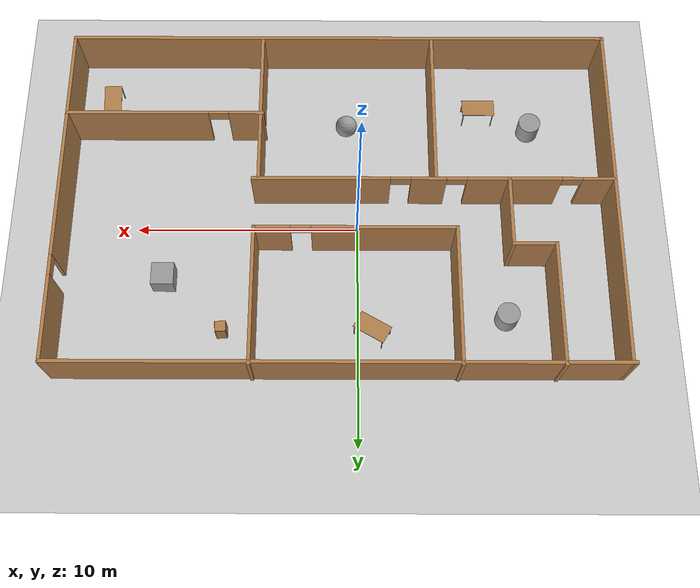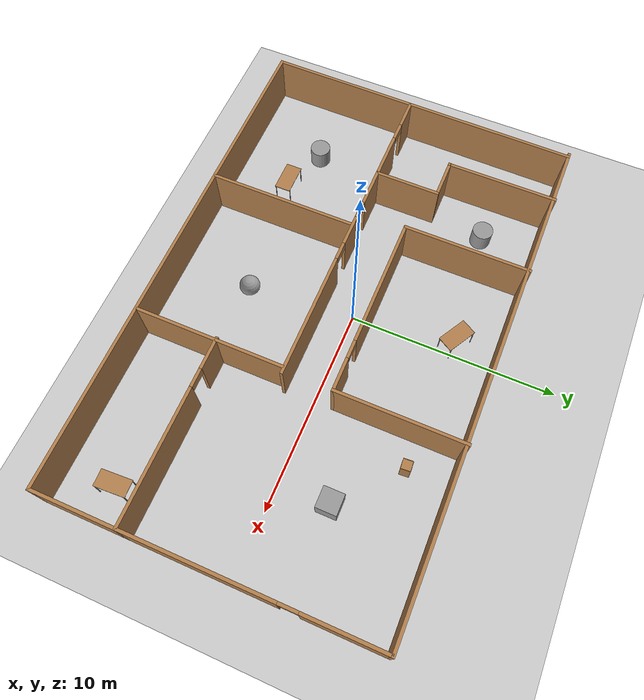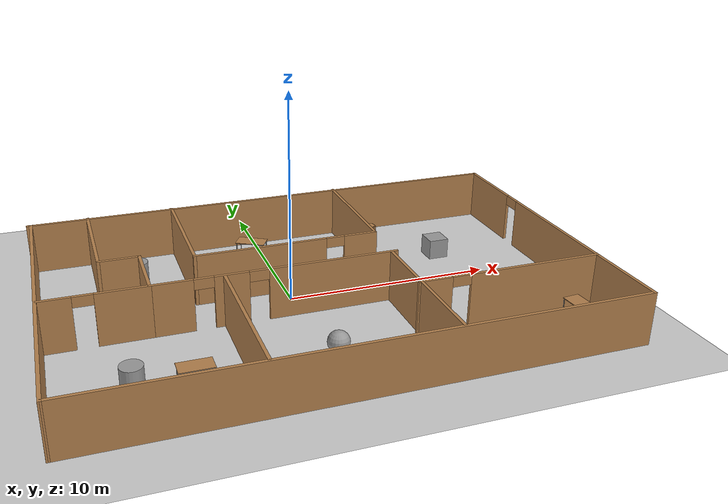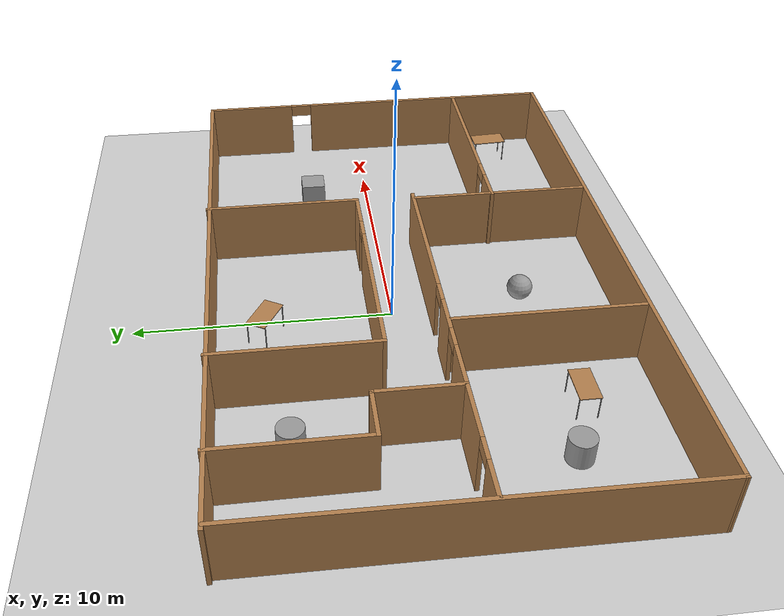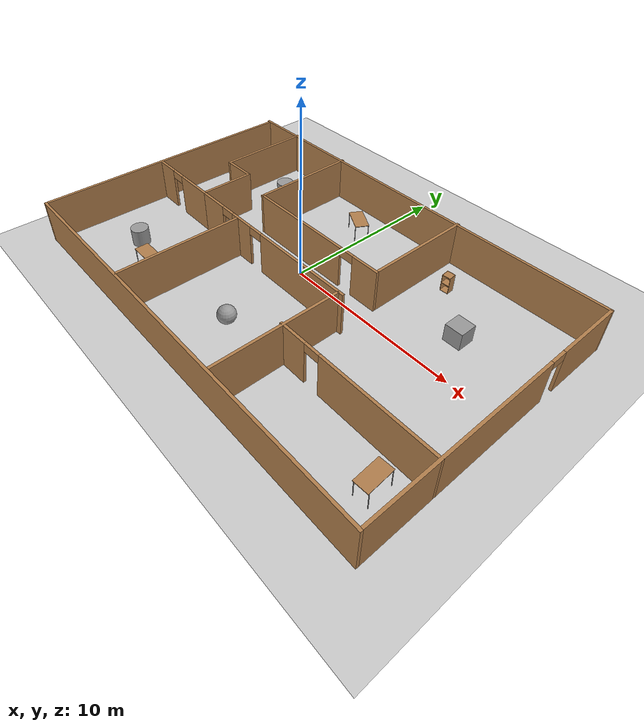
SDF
<sdf version="1.7">
 <world name="default">
  <light name="sun" type="directional">
   <pose>0 0 10 0 -0 0</pose>
   <diffuse>0.8 0.8 0.8 1</diffuse>
   <specular>0.2 0.2 0.2 1</specular>
   <attenuation>
    <range>1000</range>
    <constant>0.9</constant>
    <linear>0.01</linear>
    <quadratic>0.001</quadratic>
   </attenuation>
   <direction>-0.5 0.1 -0.9</direction>
   <spot><inner_angle>0</inner_angle><outer_angle>0</outer_angle><falloff>0</falloff></spot>
  </light>
  <model name="ground_plane">
   <static>1</static>
   <link name="link">
    <collision name="collision">
     <geometry><plane><normal>0 0 1</normal><size>100 100</size></plane></geometry>
     <surface>
      <contact><collide_bitmask>65535</collide_bitmask></contact>
      <friction><ode><mu>100</mu><mu2>50</mu2></ode></friction>
     </surface>
    </collision>
    <visual name="visual">
     <cast_shadows>0</cast_shadows>
     <geometry><plane><normal>0 0 1</normal><size>100 100</size></plane></geometry>
     <material>
      <script><uri>file://media/materials/scripts/gazebo.material</uri><name>Gazebo/Grey</name></script>
     </material>
    </visual>
   </link>
  </model>
  <gravity>0 0 -9.8</gravity>
  <magnetic_field>6e-06 2.3e-05 -4.2e-05</magnetic_field>
  <atmosphere type="adiabatic"/>
  <physics type="ode">
   <max_step_size>0.001</max_step_size>
   <real_time_factor>1</real_time_factor>
   <real_time_update_rate>1000</real_time_update_rate>
  </physics>
  <scene><ambient>0.4 0.4 0.4 1</ambient><background>0.7 0.7 0.7 1</background><shadows>1</shadows></scene>
  <spherical_coordinates>
   <surface_model>EARTH_WGS84</surface_model>
   <latitude_deg>0</latitude_deg>
   <longitude_deg>0</longitude_deg>
   <elevation>0</elevation>
   <heading_deg>0</heading_deg>
  </spherical_coordinates>
  <model name="aki_home">
   <link name="Wall_35">
    <pose>0.000337 7.80034 0 0 -0 3.14159</pose>
    <visual name="Wall_35_Visual">
     <pose>0 0 1.25 0 -0 0</pose>
     <geometry><box><size>24.75 0.15 2.5</size></box></geometry>
     <material>
      <script><uri>file://media/materials/scripts/gazebo.material</uri><name>Gazebo/Wood</name></script>
      <ambient>1 1 1 1</ambient>
      <shader type="pixel"/>
     </material>
     <meta><layer>0</layer></meta>
    </visual>
    <collision name="Wall_35_Collision">
     <pose>0 0 1.25 0 -0 0</pose>
     <geometry><box><size>24.75 0.15 2.5</size></box></geometry>
     <surface>
      <friction>
       <ode><mu>1</mu><mu2>1</mu2><fdir1>0 0 0</fdir1><slip1>0</slip1><slip2>0</slip2></ode>
       <torsional>
        <coefficient>1</coefficient>
        <patch_radius>0</patch_radius>
        <surface_radius>0</surface_radius>
        <use_patch_radius>1</use_patch_radius>
        <ode><slip>0</slip></ode>
       </torsional>
      </friction>
      <bounce><restitution_coefficient>0</restitution_coefficient><threshold>1e+06</threshold></bounce>
      <contact>
       <collide_without_contact>0</collide_without_contact>
       <collide_without_contact_bitmask>1</collide_without_contact_bitmask>
       <collide_bitmask>1</collide_bitmask>
       <ode>
        <soft_cfm>0</soft_cfm>
        <soft_erp>0.2</soft_erp>
        <kp>1e+13</kp>
        <kd>1</kd>
        <max_vel>0.01</max_vel>
        <min_depth>0</min_depth>
       </ode>
       <bullet>
        <split_impulse>1</split_impulse>
        <split_impulse_penetration_threshold>-0.01</split_impulse_penetration_threshold>
        <soft_cfm>0</soft_cfm>
        <soft_erp>0.2</soft_erp>
        <kp>1e+13</kp>
        <kd>1</kd>
       </bullet>
      </contact>
     </surface>
    </collision>
   </link>
   <link name="Wall_36">
    <pose>-12.2289 -0.035042 0 0 0 -1.57983</pose>
    <visual name="Wall_36_Visual">
     <pose>0 0 1.25 0 -0 0</pose>
     <geometry><box><size>15.8214 0.15 2.5</size></box></geometry>
     <material>
      <script><uri>file://media/materials/scripts/gazebo.material</uri><name>Gazebo/Wood</name></script>
      <ambient>1 1 1 1</ambient>
      <shader type="pixel"/>
     </material>
     <meta><layer>0</layer></meta>
    </visual>
    <collision name="Wall_36_Collision">
     <pose>0 0 1.25 0 -0 0</pose>
     <geometry><box><size>15.8214 0.15 2.5</size></box></geometry>
     <surface>
      <friction>
       <ode><mu>1</mu><mu2>1</mu2><fdir1>0 0 0</fdir1><slip1>0</slip1><slip2>0</slip2></ode>
       <torsional>
        <coefficient>1</coefficient>
        <patch_radius>0</patch_radius>
        <surface_radius>0</surface_radius>
        <use_patch_radius>1</use_patch_radius>
        <ode><slip>0</slip></ode>
       </torsional>
      </friction>
      <bounce><restitution_coefficient>0</restitution_coefficient><threshold>1e+06</threshold></bounce>
      <contact>
       <collide_without_contact>0</collide_without_contact>
       <collide_without_contact_bitmask>1</collide_without_contact_bitmask>
       <collide_bitmask>1</collide_bitmask>
       <ode>
        <soft_cfm>0</soft_cfm>
        <soft_erp>0.2</soft_erp>
        <kp>1e+13</kp>
        <kd>1</kd>
        <max_vel>0.01</max_vel>
        <min_depth>0</min_depth>
       </ode>
       <bullet>
        <split_impulse>1</split_impulse>
        <split_impulse_penetration_threshold>-0.01</split_impulse_penetration_threshold>
        <soft_cfm>0</soft_cfm>
        <soft_erp>0.2</soft_erp>
        <kp>1e+13</kp>
        <kd>1</kd>
       </bullet>
      </contact>
     </surface>
    </collision>
   </link>
   <link name="Wall_37">
    <pose>0.000337 -7.87042 0 0 -0 0</pose>
    <visual name="Wall_37_Visual">
     <pose>0 0 1.25 0 -0 0</pose>
     <geometry><box><size>24.75 0.15 2.5</size></box></geometry>
     <material>
      <script><uri>file://media/materials/scripts/gazebo.material</uri><name>Gazebo/Wood</name></script>
      <ambient>1 1 1 1</ambient>
      <shader type="pixel"/>
     </material>
     <meta><layer>0</layer></meta>
    </visual>
    <collision name="Wall_37_Collision">
     <pose>0 0 1.25 0 -0 0</pose>
     <geometry><box><size>24.75 0.15 2.5</size></box></geometry>
     <surface>
      <friction>
       <ode><mu>1</mu><mu2>1</mu2><fdir1>0 0 0</fdir1><slip1>0</slip1><slip2>0</slip2></ode>
       <torsional>
        <coefficient>1</coefficient>
        <patch_radius>0</patch_radius>
        <surface_radius>0</surface_radius>
        <use_patch_radius>1</use_patch_radius>
        <ode><slip>0</slip></ode>
       </torsional>
      </friction>
      <bounce><restitution_coefficient>0</restitution_coefficient><threshold>1e+06</threshold></bounce>
      <contact>
       <collide_without_contact>0</collide_without_contact>
       <collide_without_contact_bitmask>1</collide_without_contact_bitmask>
       <collide_bitmask>1</collide_bitmask>
       <ode>
        <soft_cfm>0</soft_cfm>
        <soft_erp>0.2</soft_erp>
        <kp>1e+13</kp>
        <kd>1</kd>
        <max_vel>0.01</max_vel>
        <min_depth>0</min_depth>
       </ode>
       <bullet>
        <split_impulse>1</split_impulse>
        <split_impulse_penetration_threshold>-0.01</split_impulse_penetration_threshold>
        <soft_cfm>0</soft_cfm>
        <soft_erp>0.2</soft_erp>
        <kp>1e+13</kp>
        <kd>1</kd>
       </bullet>
      </contact>
     </surface>
    </collision>
   </link>
   <link name="Wall_38">
    <pose>12.3003 -0.070421 0 0 -0 1.5708</pose>
    <visual name="Wall_38_Visual_0">
     <pose>-2.34983 0 1.25 0 -0 0</pose>
     <geometry><box><size>11.0503 0.15 2.5</size></box></geometry>
     <material>
      <script><uri>file://media/materials/scripts/gazebo.material</uri><name>Gazebo/Wood</name></script>
      <ambient>1 1 1 1</ambient>
      <shader type="pixel"/>
     </material>
     <meta><layer>0</layer></meta>
    </visual>
    <visual name="Wall_38_Visual_1">
     <pose>5.97517 0 1.25 0 -0 0</pose>
     <geometry><box><size>3.79967 0.15 2.5</size></box></geometry>
     <material>
      <script><uri>file://media/materials/scripts/gazebo.material</uri><name>Gazebo/Wood</name></script>
      <ambient>1 1 1 1</ambient>
      <shader type="pixel"/>
     </material>
     <meta><layer>0</layer></meta>
    </visual>
    <visual name="Wall_38_Visual_2">
     <pose>3.62533 0 2.25 0 -0 0</pose>
     <geometry><box><size>0.9 0.15 0.5</size></box></geometry>
     <material>
      <script><uri>file://media/materials/scripts/gazebo.material</uri><name>Gazebo/Wood</name></script>
      <ambient>1 1 1 1</ambient>
      <shader type="pixel"/>
     </material>
     <meta><layer>0</layer></meta>
    </visual>
    <collision name="Wall_38_Collision_0">
     <pose>-2.34983 0 1.25 0 -0 0</pose>
     <geometry><box><size>11.0503 0.15 2.5</size></box></geometry>
     <surface>
      <friction>
       <ode><mu>1</mu><mu2>1</mu2><fdir1>0 0 0</fdir1><slip1>0</slip1><slip2>0</slip2></ode>
       <torsional>
        <coefficient>1</coefficient>
        <patch_radius>0</patch_radius>
        <surface_radius>0</surface_radius>
        <use_patch_radius>1</use_patch_radius>
        <ode><slip>0</slip></ode>
       </torsional>
      </friction>
      <bounce><restitution_coefficient>0</restitution_coefficient><threshold>1e+06</threshold></bounce>
      <contact>
       <collide_without_contact>0</collide_without_contact>
       <collide_without_contact_bitmask>1</collide_without_contact_bitmask>
       <collide_bitmask>1</collide_bitmask>
       <ode>
        <soft_cfm>0</soft_cfm>
        <soft_erp>0.2</soft_erp>
        <kp>1e+13</kp>
        <kd>1</kd>
        <max_vel>0.01</max_vel>
        <min_depth>0</min_depth>
       </ode>
       <bullet>
        <split_impulse>1</split_impulse>
        <split_impulse_penetration_threshold>-0.01</split_impulse_penetration_threshold>
        <soft_cfm>0</soft_cfm>
        <soft_erp>0.2</soft_erp>
        <kp>1e+13</kp>
        <kd>1</kd>
       </bullet>
      </contact>
     </surface>
    </collision>
    <collision name="Wall_38_Collision_1">
     <pose>5.97517 0 1.25 0 -0 0</pose>
     <geometry><box><size>3.79967 0.15 2.5</size></box></geometry>
     <surface>
      <friction>
       <ode><mu>1</mu><mu2>1</mu2><fdir1>0 0 0</fdir1><slip1>0</slip1><slip2>0</slip2></ode>
       <torsional>
        <coefficient>1</coefficient>
        <patch_radius>0</patch_radius>
        <surface_radius>0</surface_radius>
        <use_patch_radius>1</use_patch_radius>
        <ode><slip>0</slip></ode>
       </torsional>
      </friction>
      <bounce><restitution_coefficient>0</restitution_coefficient><threshold>1e+06</threshold></bounce>
      <contact>
       <collide_without_contact>0</collide_without_contact>
       <collide_without_contact_bitmask>1</collide_without_contact_bitmask>
       <collide_bitmask>1</collide_bitmask>
       <ode>
        <soft_cfm>0</soft_cfm>
        <soft_erp>0.2</soft_erp>
        <kp>1e+13</kp>
        <kd>1</kd>
        <max_vel>0.01</max_vel>
        <min_depth>0</min_depth>
       </ode>
       <bullet>
        <split_impulse>1</split_impulse>
        <split_impulse_penetration_threshold>-0.01</split_impulse_penetration_threshold>
        <soft_cfm>0</soft_cfm>
        <soft_erp>0.2</soft_erp>
        <kp>1e+13</kp>
        <kd>1</kd>
       </bullet>
      </contact>
     </surface>
    </collision>
    <collision name="Wall_38_Collision_2">
     <pose>3.62533 0 2.25 0 -0 0</pose>
     <geometry><box><size>0.9 0.15 0.5</size></box></geometry>
     <surface>
      <friction>
       <ode><mu>1</mu><mu2>1</mu2><fdir1>0 0 0</fdir1><slip1>0</slip1><slip2>0</slip2></ode>
       <torsional>
        <coefficient>1</coefficient>
        <patch_radius>0</patch_radius>
        <surface_radius>0</surface_radius>
        <use_patch_radius>1</use_patch_radius>
        <ode><slip>0</slip></ode>
       </torsional>
      </friction>
      <bounce><restitution_coefficient>0</restitution_coefficient><threshold>1e+06</threshold></bounce>
      <contact>
       <collide_without_contact>0</collide_without_contact>
       <collide_without_contact_bitmask>1</collide_without_contact_bitmask>
       <collide_bitmask>1</collide_bitmask>
       <ode>
        <soft_cfm>0</soft_cfm>
        <soft_erp>0.2</soft_erp>
        <kp>1e+13</kp>
        <kd>1</kd>
        <max_vel>0.01</max_vel>
        <min_depth>0</min_depth>
       </ode>
       <bullet>
        <split_impulse>1</split_impulse>
        <split_impulse_penetration_threshold>-0.01</split_impulse_penetration_threshold>
        <soft_cfm>0</soft_cfm>
        <soft_erp>0.2</soft_erp>
        <kp>1e+13</kp>
        <kd>1</kd>
       </bullet>
      </contact>
     </surface>
    </collision>
   </link>
   <link name="Wall_40">
    <pose>3.66798 4.82109 0 0 0 -1.5708</pose>
    <visual name="Wall_40_Visual">
     <pose>0 0 1.25 0 -0 0</pose>
     <geometry><box><size>6.25 0.15 2.5</size></box></geometry>
     <material>
      <script><uri>file://media/materials/scripts/gazebo.material</uri><name>Gazebo/Wood</name></script>
      <ambient>1 1 1 1</ambient>
      <shader type="pixel"/>
     </material>
     <meta><layer>0</layer></meta>
    </visual>
    <collision name="Wall_40_Collision">
     <pose>0 0 1.25 0 -0 0</pose>
     <geometry><box><size>6.25 0.15 2.5</size></box></geometry>
     <surface>
      <friction>
       <ode><mu>1</mu><mu2>1</mu2><fdir1>0 0 0</fdir1><slip1>0</slip1><slip2>0</slip2></ode>
       <torsional>
        <coefficient>1</coefficient>
        <patch_radius>0</patch_radius>
        <surface_radius>0</surface_radius>
        <use_patch_radius>1</use_patch_radius>
        <ode><slip>0</slip></ode>
       </torsional>
      </friction>
      <bounce><restitution_coefficient>0</restitution_coefficient><threshold>1e+06</threshold></bounce>
      <contact>
       <collide_without_contact>0</collide_without_contact>
       <collide_without_contact_bitmask>1</collide_without_contact_bitmask>
       <collide_bitmask>1</collide_bitmask>
       <ode>
        <soft_cfm>0</soft_cfm>
        <soft_erp>0.2</soft_erp>
        <kp>1e+13</kp>
        <kd>1</kd>
        <max_vel>0.01</max_vel>
        <min_depth>0</min_depth>
       </ode>
       <bullet>
        <split_impulse>1</split_impulse>
        <split_impulse_penetration_threshold>-0.01</split_impulse_penetration_threshold>
        <soft_cfm>0</soft_cfm>
        <soft_erp>0.2</soft_erp>
        <kp>1e+13</kp>
        <kd>1</kd>
       </bullet>
      </contact>
     </surface>
    </collision>
   </link>
   <link name="Wall_41">
    <pose>-0.757024 1.77109 0 0 -0 3.14159</pose>
    <visual name="Wall_41_Visual_0">
     <pose>-3.66152 0 1.25 0 -0 0</pose>
     <geometry><box><size>1.67695 0.15 2.5</size></box></geometry>
     <material>
      <script><uri>file://media/materials/scripts/gazebo.material</uri><name>Gazebo/Wood</name></script>
      <ambient>1 1 1 1</ambient>
      <shader type="pixel"/>
     </material>
     <meta><layer>0</layer></meta>
    </visual>
    <visual name="Wall_41_Visual_1">
     <pose>1.28848 0 1.25 0 -0 0</pose>
     <geometry><box><size>6.42305 0.15 2.5</size></box></geometry>
     <material>
      <script><uri>file://media/materials/scripts/gazebo.material</uri><name>Gazebo/Wood</name></script>
      <ambient>1 1 1 1</ambient>
      <shader type="pixel"/>
     </material>
     <meta><layer>0</layer></meta>
    </visual>
    <visual name="Wall_41_Visual_2">
     <pose>-2.37304 0 2.25 0 -0 0</pose>
     <geometry><box><size>0.9 0.15 0.5</size></box></geometry>
     <material>
      <script><uri>file://media/materials/scripts/gazebo.material</uri><name>Gazebo/Wood</name></script>
      <ambient>1 1 1 1</ambient>
      <shader type="pixel"/>
     </material>
     <meta><layer>0</layer></meta>
    </visual>
    <collision name="Wall_41_Collision_0">
     <pose>-3.66152 0 1.25 0 -0 0</pose>
     <geometry><box><size>1.67695 0.15 2.5</size></box></geometry>
     <surface>
      <friction>
       <ode><mu>1</mu><mu2>1</mu2><fdir1>0 0 0</fdir1><slip1>0</slip1><slip2>0</slip2></ode>
       <torsional>
        <coefficient>1</coefficient>
        <patch_radius>0</patch_radius>
        <surface_radius>0</surface_radius>
        <use_patch_radius>1</use_patch_radius>
        <ode><slip>0</slip></ode>
       </torsional>
      </friction>
      <bounce><restitution_coefficient>0</restitution_coefficient><threshold>1e+06</threshold></bounce>
      <contact>
       <collide_without_contact>0</collide_without_contact>
       <collide_without_contact_bitmask>1</collide_without_contact_bitmask>
       <collide_bitmask>1</collide_bitmask>
       <ode>
        <soft_cfm>0</soft_cfm>
        <soft_erp>0.2</soft_erp>
        <kp>1e+13</kp>
        <kd>1</kd>
        <max_vel>0.01</max_vel>
        <min_depth>0</min_depth>
       </ode>
       <bullet>
        <split_impulse>1</split_impulse>
        <split_impulse_penetration_threshold>-0.01</split_impulse_penetration_threshold>
        <soft_cfm>0</soft_cfm>
        <soft_erp>0.2</soft_erp>
        <kp>1e+13</kp>
        <kd>1</kd>
       </bullet>
      </contact>
     </surface>
    </collision>
    <collision name="Wall_41_Collision_1">
     <pose>1.28848 0 1.25 0 -0 0</pose>
     <geometry><box><size>6.42305 0.15 2.5</size></box></geometry>
     <surface>
      <friction>
       <ode><mu>1</mu><mu2>1</mu2><fdir1>0 0 0</fdir1><slip1>0</slip1><slip2>0</slip2></ode>
       <torsional>
        <coefficient>1</coefficient>
        <patch_radius>0</patch_radius>
        <surface_radius>0</surface_radius>
        <use_patch_radius>1</use_patch_radius>
        <ode><slip>0</slip></ode>
       </torsional>
      </friction>
      <bounce><restitution_coefficient>0</restitution_coefficient><threshold>1e+06</threshold></bounce>
      <contact>
       <collide_without_contact>0</collide_without_contact>
       <collide_without_contact_bitmask>1</collide_without_contact_bitmask>
       <collide_bitmask>1</collide_bitmask>
       <ode>
        <soft_cfm>0</soft_cfm>
        <soft_erp>0.2</soft_erp>
        <kp>1e+13</kp>
        <kd>1</kd>
        <max_vel>0.01</max_vel>
        <min_depth>0</min_depth>
       </ode>
       <bullet>
        <split_impulse>1</split_impulse>
        <split_impulse_penetration_threshold>-0.01</split_impulse_penetration_threshold>
        <soft_cfm>0</soft_cfm>
        <soft_erp>0.2</soft_erp>
        <kp>1e+13</kp>
        <kd>1</kd>
       </bullet>
      </contact>
     </surface>
    </collision>
    <collision name="Wall_41_Collision_2">
     <pose>-2.37304 0 2.25 0 -0 0</pose>
     <geometry><box><size>0.9 0.15 0.5</size></box></geometry>
     <surface>
      <friction>
       <ode><mu>1</mu><mu2>1</mu2><fdir1>0 0 0</fdir1><slip1>0</slip1><slip2>0</slip2></ode>
       <torsional>
        <coefficient>1</coefficient>
        <patch_radius>0</patch_radius>
        <surface_radius>0</surface_radius>
        <use_patch_radius>1</use_patch_radius>
        <ode><slip>0</slip></ode>
       </torsional>
      </friction>
      <bounce><restitution_coefficient>0</restitution_coefficient><threshold>1e+06</threshold></bounce>
      <contact>
       <collide_without_contact>0</collide_without_contact>
       <collide_without_contact_bitmask>1</collide_without_contact_bitmask>
       <collide_bitmask>1</collide_bitmask>
       <ode>
        <soft_cfm>0</soft_cfm>
        <soft_erp>0.2</soft_erp>
        <kp>1e+13</kp>
        <kd>1</kd>
        <max_vel>0.01</max_vel>
        <min_depth>0</min_depth>
       </ode>
       <bullet>
        <split_impulse>1</split_impulse>
        <split_impulse_penetration_threshold>-0.01</split_impulse_penetration_threshold>
        <soft_cfm>0</soft_cfm>
        <soft_erp>0.2</soft_erp>
        <kp>1e+13</kp>
        <kd>1</kd>
       </bullet>
      </contact>
     </surface>
    </collision>
   </link>
   <link name="Wall_42">
    <pose>-5.18202 4.82109 0 0 -0 1.5708</pose>
    <visual name="Wall_42_Visual">
     <pose>0 0 1.25 0 -0 0</pose>
     <geometry><box><size>6.25 0.15 2.5</size></box></geometry>
     <material>
      <script><uri>file://media/materials/scripts/gazebo.material</uri><name>Gazebo/Wood</name></script>
      <ambient>1 1 1 1</ambient>
      <shader type="pixel"/>
     </material>
     <meta><layer>0</layer></meta>
    </visual>
    <collision name="Wall_42_Collision">
     <pose>0 0 1.25 0 -0 0</pose>
     <geometry><box><size>6.25 0.15 2.5</size></box></geometry>
     <surface>
      <friction>
       <ode><mu>1</mu><mu2>1</mu2><fdir1>0 0 0</fdir1><slip1>0</slip1><slip2>0</slip2></ode>
       <torsional>
        <coefficient>1</coefficient>
        <patch_radius>0</patch_radius>
        <surface_radius>0</surface_radius>
        <use_patch_radius>1</use_patch_radius>
        <ode><slip>0</slip></ode>
       </torsional>
      </friction>
      <bounce><restitution_coefficient>0</restitution_coefficient><threshold>1e+06</threshold></bounce>
      <contact>
       <collide_without_contact>0</collide_without_contact>
       <collide_without_contact_bitmask>1</collide_without_contact_bitmask>
       <collide_bitmask>1</collide_bitmask>
       <ode>
        <soft_cfm>0</soft_cfm>
        <soft_erp>0.2</soft_erp>
        <kp>1e+13</kp>
        <kd>1</kd>
        <max_vel>0.01</max_vel>
        <min_depth>0</min_depth>
       </ode>
       <bullet>
        <split_impulse>1</split_impulse>
        <split_impulse_penetration_threshold>-0.01</split_impulse_penetration_threshold>
        <soft_cfm>0</soft_cfm>
        <soft_erp>0.2</soft_erp>
        <kp>1e+13</kp>
        <kd>1</kd>
       </bullet>
      </contact>
     </surface>
    </collision>
   </link>
   <link name="Wall_49">
    <pose>-4.32757 -4.24051 0 0 0 -1.5708</pose>
    <visual name="Wall_49_Visual">
     <pose>0 0 1.25 0 -0 0</pose>
     <geometry><box><size>7.25 0.15 2.5</size></box></geometry>
     <material>
      <script><uri>file://media/materials/scripts/gazebo.material</uri><name>Gazebo/Wood</name></script>
      <ambient>1 1 1 1</ambient>
      <shader type="pixel"/>
     </material>
     <meta><layer>0</layer></meta>
    </visual>
    <collision name="Wall_49_Collision">
     <pose>0 0 1.25 0 -0 0</pose>
     <geometry><box><size>7.25 0.15 2.5</size></box></geometry>
     <surface>
      <friction>
       <ode><mu>1</mu><mu2>1</mu2><fdir1>0 0 0</fdir1><slip1>0</slip1><slip2>0</slip2></ode>
       <torsional>
        <coefficient>1</coefficient>
        <patch_radius>0</patch_radius>
        <surface_radius>0</surface_radius>
        <use_patch_radius>1</use_patch_radius>
        <ode><slip>0</slip></ode>
       </torsional>
      </friction>
      <bounce><restitution_coefficient>0</restitution_coefficient><threshold>1e+06</threshold></bounce>
      <contact>
       <collide_without_contact>0</collide_without_contact>
       <collide_without_contact_bitmask>1</collide_without_contact_bitmask>
       <collide_bitmask>1</collide_bitmask>
       <ode>
        <soft_cfm>0</soft_cfm>
        <soft_erp>0.2</soft_erp>
        <kp>1e+13</kp>
        <kd>1</kd>
        <max_vel>0.01</max_vel>
        <min_depth>0</min_depth>
       </ode>
       <bullet>
        <split_impulse>1</split_impulse>
        <split_impulse_penetration_threshold>-0.01</split_impulse_penetration_threshold>
        <soft_cfm>0</soft_cfm>
        <soft_erp>0.2</soft_erp>
        <kp>1e+13</kp>
        <kd>1</kd>
       </bullet>
      </contact>
     </surface>
    </collision>
   </link>
   <link name="Wall_51">
    <pose>3.52646 -4.21622 0 0 -0 1.5708</pose>
    <visual name="Wall_51_Visual">
     <pose>0 0 1.25 0 -0 0</pose>
     <geometry><box><size>7.25 0.15 2.5</size></box></geometry>
     <material>
      <script><uri>file://media/materials/scripts/gazebo.material</uri><name>Gazebo/Wood</name></script>
      <ambient>1 1 1 1</ambient>
      <shader type="pixel"/>
     </material>
     <meta><layer>0</layer></meta>
    </visual>
    <collision name="Wall_51_Collision">
     <pose>0 0 1.25 0 -0 0</pose>
     <geometry><box><size>7.25 0.15 2.5</size></box></geometry>
     <surface>
      <friction>
       <ode><mu>1</mu><mu2>1</mu2><fdir1>0 0 0</fdir1><slip1>0</slip1><slip2>0</slip2></ode>
       <torsional>
        <coefficient>1</coefficient>
        <patch_radius>0</patch_radius>
        <surface_radius>0</surface_radius>
        <use_patch_radius>1</use_patch_radius>
        <ode><slip>0</slip></ode>
       </torsional>
      </friction>
      <bounce><restitution_coefficient>0</restitution_coefficient><threshold>1e+06</threshold></bounce>
      <contact>
       <collide_without_contact>0</collide_without_contact>
       <collide_without_contact_bitmask>1</collide_without_contact_bitmask>
       <collide_bitmask>1</collide_bitmask>
       <ode>
        <soft_cfm>0</soft_cfm>
        <soft_erp>0.2</soft_erp>
        <kp>1e+13</kp>
        <kd>1</kd>
        <max_vel>0.01</max_vel>
        <min_depth>0</min_depth>
       </ode>
       <bullet>
        <split_impulse>1</split_impulse>
        <split_impulse_penetration_threshold>-0.01</split_impulse_penetration_threshold>
        <soft_cfm>0</soft_cfm>
        <soft_erp>0.2</soft_erp>
        <kp>1e+13</kp>
        <kd>1</kd>
       </bullet>
      </contact>
     </surface>
    </collision>
   </link>
   <link name="Wall_54">
    <pose>7.87534 -3.87458 0 0 -0 3.14159</pose>
    <visual name="Wall_54_Visual_0">
     <pose>-1.25578 0 1.25 0 -0 0</pose>
     <geometry><box><size>6.48843 0.15 2.5</size></box></geometry>
     <material>
      <script><uri>file://media/materials/scripts/gazebo.material</uri><name>Gazebo/Wood</name></script>
      <ambient>1 1 1 1</ambient>
      <shader type="pixel"/>
     </material>
     <meta><layer>0</layer></meta>
    </visual>
    <visual name="Wall_54_Visual_1">
     <pose>3.69422 0 1.25 0 -0 0</pose>
     <geometry><box><size>1.61157 0.15 2.5</size></box></geometry>
     <material>
      <script><uri>file://media/materials/scripts/gazebo.material</uri><name>Gazebo/Wood</name></script>
      <ambient>1 1 1 1</ambient>
      <shader type="pixel"/>
     </material>
     <meta><layer>0</layer></meta>
    </visual>
    <visual name="Wall_54_Visual_2">
     <pose>2.43843 0 2.25 0 -0 0</pose>
     <geometry><box><size>0.9 0.15 0.5</size></box></geometry>
     <material>
      <script><uri>file://media/materials/scripts/gazebo.material</uri><name>Gazebo/Wood</name></script>
      <ambient>1 1 1 1</ambient>
      <shader type="pixel"/>
     </material>
     <meta><layer>0</layer></meta>
    </visual>
    <collision name="Wall_54_Collision_0">
     <pose>-1.25578 0 1.25 0 -0 0</pose>
     <geometry><box><size>6.48843 0.15 2.5</size></box></geometry>
     <surface>
      <friction>
       <ode><mu>1</mu><mu2>1</mu2><fdir1>0 0 0</fdir1><slip1>0</slip1><slip2>0</slip2></ode>
       <torsional>
        <coefficient>1</coefficient>
        <patch_radius>0</patch_radius>
        <surface_radius>0</surface_radius>
        <use_patch_radius>1</use_patch_radius>
        <ode><slip>0</slip></ode>
       </torsional>
      </friction>
      <bounce><restitution_coefficient>0</restitution_coefficient><threshold>1e+06</threshold></bounce>
      <contact>
       <collide_without_contact>0</collide_without_contact>
       <collide_without_contact_bitmask>1</collide_without_contact_bitmask>
       <collide_bitmask>1</collide_bitmask>
       <ode>
        <soft_cfm>0</soft_cfm>
        <soft_erp>0.2</soft_erp>
        <kp>1e+13</kp>
        <kd>1</kd>
        <max_vel>0.01</max_vel>
        <min_depth>0</min_depth>
       </ode>
       <bullet>
        <split_impulse>1</split_impulse>
        <split_impulse_penetration_threshold>-0.01</split_impulse_penetration_threshold>
        <soft_cfm>0</soft_cfm>
        <soft_erp>0.2</soft_erp>
        <kp>1e+13</kp>
        <kd>1</kd>
       </bullet>
      </contact>
     </surface>
    </collision>
    <collision name="Wall_54_Collision_1">
     <pose>3.69422 0 1.25 0 -0 0</pose>
     <geometry><box><size>1.61157 0.15 2.5</size></box></geometry>
     <surface>
      <friction>
       <ode><mu>1</mu><mu2>1</mu2><fdir1>0 0 0</fdir1><slip1>0</slip1><slip2>0</slip2></ode>
       <torsional>
        <coefficient>1</coefficient>
        <patch_radius>0</patch_radius>
        <surface_radius>0</surface_radius>
        <use_patch_radius>1</use_patch_radius>
        <ode><slip>0</slip></ode>
       </torsional>
      </friction>
      <bounce><restitution_coefficient>0</restitution_coefficient><threshold>1e+06</threshold></bounce>
      <contact>
       <collide_without_contact>0</collide_without_contact>
       <collide_without_contact_bitmask>1</collide_without_contact_bitmask>
       <collide_bitmask>1</collide_bitmask>
       <ode>
        <soft_cfm>0</soft_cfm>
        <soft_erp>0.2</soft_erp>
        <kp>1e+13</kp>
        <kd>1</kd>
        <max_vel>0.01</max_vel>
        <min_depth>0</min_depth>
       </ode>
       <bullet>
        <split_impulse>1</split_impulse>
        <split_impulse_penetration_threshold>-0.01</split_impulse_penetration_threshold>
        <soft_cfm>0</soft_cfm>
        <soft_erp>0.2</soft_erp>
        <kp>1e+13</kp>
        <kd>1</kd>
       </bullet>
      </contact>
     </surface>
    </collision>
    <collision name="Wall_54_Collision_2">
     <pose>2.43843 0 2.25 0 -0 0</pose>
     <geometry><box><size>0.9 0.15 0.5</size></box></geometry>
     <surface>
      <friction>
       <ode><mu>1</mu><mu2>1</mu2><fdir1>0 0 0</fdir1><slip1>0</slip1><slip2>0</slip2></ode>
       <torsional>
        <coefficient>1</coefficient>
        <patch_radius>0</patch_radius>
        <surface_radius>0</surface_radius>
        <use_patch_radius>1</use_patch_radius>
        <ode><slip>0</slip></ode>
       </torsional>
      </friction>
      <bounce><restitution_coefficient>0</restitution_coefficient><threshold>1e+06</threshold></bounce>
      <contact>
       <collide_without_contact>0</collide_without_contact>
       <collide_without_contact_bitmask>1</collide_without_contact_bitmask>
       <collide_bitmask>1</collide_bitmask>
       <ode>
        <soft_cfm>0</soft_cfm>
        <soft_erp>0.2</soft_erp>
        <kp>1e+13</kp>
        <kd>1</kd>
        <max_vel>0.01</max_vel>
        <min_depth>0</min_depth>
       </ode>
       <bullet>
        <split_impulse>1</split_impulse>
        <split_impulse_penetration_threshold>-0.01</split_impulse_penetration_threshold>
        <soft_cfm>0</soft_cfm>
        <soft_erp>0.2</soft_erp>
        <kp>1e+13</kp>
        <kd>1</kd>
       </bullet>
      </contact>
     </surface>
    </collision>
   </link>
   <link name="Wall_56">
    <pose>-9.42208 5.19609 0 0 0 -1.5708</pose>
    <visual name="Wall_56_Visual">
     <pose>0 0 1.25 0 -0 0</pose>
     <geometry><box><size>5.5 0.15 2.5</size></box></geometry>
     <material>
      <script><uri>file://media/materials/scripts/gazebo.material</uri><name>Gazebo/Wood</name></script>
      <ambient>1 1 1 1</ambient>
      <shader type="pixel"/>
     </material>
     <meta><layer>0</layer></meta>
    </visual>
    <collision name="Wall_56_Collision">
     <pose>0 0 1.25 0 -0 0</pose>
     <geometry><box><size>5.5 0.15 2.5</size></box></geometry>
     <surface>
      <friction>
       <ode><mu>1</mu><mu2>1</mu2><fdir1>0 0 0</fdir1><slip1>0</slip1><slip2>0</slip2></ode>
       <torsional>
        <coefficient>1</coefficient>
        <patch_radius>0</patch_radius>
        <surface_radius>0</surface_radius>
        <use_patch_radius>1</use_patch_radius>
        <ode><slip>0</slip></ode>
       </torsional>
      </friction>
      <bounce><restitution_coefficient>0</restitution_coefficient><threshold>1e+06</threshold></bounce>
      <contact>
       <collide_without_contact>0</collide_without_contact>
       <collide_without_contact_bitmask>1</collide_without_contact_bitmask>
       <collide_bitmask>1</collide_bitmask>
       <ode>
        <soft_cfm>0</soft_cfm>
        <soft_erp>0.2</soft_erp>
        <kp>1e+13</kp>
        <kd>1</kd>
        <max_vel>0.01</max_vel>
        <min_depth>0</min_depth>
       </ode>
       <bullet>
        <split_impulse>1</split_impulse>
        <split_impulse_penetration_threshold>-0.01</split_impulse_penetration_threshold>
        <soft_cfm>0</soft_cfm>
        <soft_erp>0.2</soft_erp>
        <kp>1e+13</kp>
        <kd>1</kd>
       </bullet>
      </contact>
     </surface>
    </collision>
   </link>
   <link name="Wall_57">
    <pose>-8.49708 2.52109 0 0 -0 0</pose>
    <visual name="Wall_57_Visual">
     <pose>0 0 1.25 0 -0 0</pose>
     <geometry><box><size>2 0.15 2.5</size></box></geometry>
     <material>
      <script><uri>file://media/materials/scripts/gazebo.material</uri><name>Gazebo/Wood</name></script>
      <ambient>1 1 1 1</ambient>
      <shader type="pixel"/>
     </material>
     <meta><layer>0</layer></meta>
    </visual>
    <collision name="Wall_57_Collision">
     <pose>0 0 1.25 0 -0 0</pose>
     <geometry><box><size>2 0.15 2.5</size></box></geometry>
     <surface>
      <friction>
       <ode><mu>1</mu><mu2>1</mu2><fdir1>0 0 0</fdir1><slip1>0</slip1><slip2>0</slip2></ode>
       <torsional>
        <coefficient>1</coefficient>
        <patch_radius>0</patch_radius>
        <surface_radius>0</surface_radius>
        <use_patch_radius>1</use_patch_radius>
        <ode><slip>0</slip></ode>
       </torsional>
      </friction>
      <bounce><restitution_coefficient>0</restitution_coefficient><threshold>1e+06</threshold></bounce>
      <contact>
       <collide_without_contact>0</collide_without_contact>
       <collide_without_contact_bitmask>1</collide_without_contact_bitmask>
       <collide_bitmask>1</collide_bitmask>
       <ode>
        <soft_cfm>0</soft_cfm>
        <soft_erp>0.2</soft_erp>
        <kp>1e+13</kp>
        <kd>1</kd>
        <max_vel>0.01</max_vel>
        <min_depth>0</min_depth>
       </ode>
       <bullet>
        <split_impulse>1</split_impulse>
        <split_impulse_penetration_threshold>-0.01</split_impulse_penetration_threshold>
        <soft_cfm>0</soft_cfm>
        <soft_erp>0.2</soft_erp>
        <kp>1e+13</kp>
        <kd>1</kd>
       </bullet>
      </contact>
     </surface>
    </collision>
   </link>
   <link name="Wall_58">
    <pose>-7.57208 0.971093 0 0 0 -1.5708</pose>
    <visual name="Wall_58_Visual">
     <pose>0 0 1.25 0 -0 0</pose>
     <geometry><box><size>3.25 0.15 2.5</size></box></geometry>
     <material>
      <script><uri>file://media/materials/scripts/gazebo.material</uri><name>Gazebo/Wood</name></script>
      <ambient>1 1 1 1</ambient>
      <shader type="pixel"/>
     </material>
     <meta><layer>0</layer></meta>
    </visual>
    <collision name="Wall_58_Collision">
     <pose>0 0 1.25 0 -0 0</pose>
     <geometry><box><size>3.25 0.15 2.5</size></box></geometry>
     <surface>
      <friction>
       <ode><mu>1</mu><mu2>1</mu2><fdir1>0 0 0</fdir1><slip1>0</slip1><slip2>0</slip2></ode>
       <torsional>
        <coefficient>1</coefficient>
        <patch_radius>0</patch_radius>
        <surface_radius>0</surface_radius>
        <use_patch_radius>1</use_patch_radius>
        <ode><slip>0</slip></ode>
       </torsional>
      </friction>
      <bounce><restitution_coefficient>0</restitution_coefficient><threshold>1e+06</threshold></bounce>
      <contact>
       <collide_without_contact>0</collide_without_contact>
       <collide_without_contact_bitmask>1</collide_without_contact_bitmask>
       <collide_bitmask>1</collide_bitmask>
       <ode>
        <soft_cfm>0</soft_cfm>
        <soft_erp>0.2</soft_erp>
        <kp>1e+13</kp>
        <kd>1</kd>
        <max_vel>0.01</max_vel>
        <min_depth>0</min_depth>
       </ode>
       <bullet>
        <split_impulse>1</split_impulse>
        <split_impulse_penetration_threshold>-0.01</split_impulse_penetration_threshold>
        <soft_cfm>0</soft_cfm>
        <soft_erp>0.2</soft_erp>
        <kp>1e+13</kp>
        <kd>1</kd>
       </bullet>
      </contact>
     </surface>
    </collision>
   </link>
   <link name="Wall_59">
    <pose>-9.87208 -0.578907 0 0 -0 3.14159</pose>
    <visual name="Wall_59_Visual_0">
     <pose>-1.17758 0 1.25 0 -0 0</pose>
     <geometry><box><size>2.39484 0.15 2.5</size></box></geometry>
     <material>
      <script><uri>file://media/materials/scripts/gazebo.material</uri><name>Gazebo/Wood</name></script>
      <ambient>1 1 1 1</ambient>
      <shader type="pixel"/>
     </material>
     <meta><layer>0</layer></meta>
    </visual>
    <visual name="Wall_59_Visual_1">
     <pose>1.64742 0 1.25 0 -0 0</pose>
     <geometry><box><size>1.45516 0.15 2.5</size></box></geometry>
     <material>
      <script><uri>file://media/materials/scripts/gazebo.material</uri><name>Gazebo/Wood</name></script>
      <ambient>1 1 1 1</ambient>
      <shader type="pixel"/>
     </material>
     <meta><layer>0</layer></meta>
    </visual>
    <visual name="Wall_59_Visual_2">
     <pose>0.469842 0 2.25 0 -0 0</pose>
     <geometry><box><size>0.9 0.15 0.5</size></box></geometry>
     <material>
      <script><uri>file://media/materials/scripts/gazebo.material</uri><name>Gazebo/Wood</name></script>
      <ambient>1 1 1 1</ambient>
      <shader type="pixel"/>
     </material>
     <meta><layer>0</layer></meta>
    </visual>
    <collision name="Wall_59_Collision_0">
     <pose>-1.17758 0 1.25 0 -0 0</pose>
     <geometry><box><size>2.39484 0.15 2.5</size></box></geometry>
     <surface>
      <friction>
       <ode><mu>1</mu><mu2>1</mu2><fdir1>0 0 0</fdir1><slip1>0</slip1><slip2>0</slip2></ode>
       <torsional>
        <coefficient>1</coefficient>
        <patch_radius>0</patch_radius>
        <surface_radius>0</surface_radius>
        <use_patch_radius>1</use_patch_radius>
        <ode><slip>0</slip></ode>
       </torsional>
      </friction>
      <bounce><restitution_coefficient>0</restitution_coefficient><threshold>1e+06</threshold></bounce>
      <contact>
       <collide_without_contact>0</collide_without_contact>
       <collide_without_contact_bitmask>1</collide_without_contact_bitmask>
       <collide_bitmask>1</collide_bitmask>
       <ode>
        <soft_cfm>0</soft_cfm>
        <soft_erp>0.2</soft_erp>
        <kp>1e+13</kp>
        <kd>1</kd>
        <max_vel>0.01</max_vel>
        <min_depth>0</min_depth>
       </ode>
       <bullet>
        <split_impulse>1</split_impulse>
        <split_impulse_penetration_threshold>-0.01</split_impulse_penetration_threshold>
        <soft_cfm>0</soft_cfm>
        <soft_erp>0.2</soft_erp>
        <kp>1e+13</kp>
        <kd>1</kd>
       </bullet>
      </contact>
     </surface>
    </collision>
    <collision name="Wall_59_Collision_1">
     <pose>1.64742 0 1.25 0 -0 0</pose>
     <geometry><box><size>1.45516 0.15 2.5</size></box></geometry>
     <surface>
      <friction>
       <ode><mu>1</mu><mu2>1</mu2><fdir1>0 0 0</fdir1><slip1>0</slip1><slip2>0</slip2></ode>
       <torsional>
        <coefficient>1</coefficient>
        <patch_radius>0</patch_radius>
        <surface_radius>0</surface_radius>
        <use_patch_radius>1</use_patch_radius>
        <ode><slip>0</slip></ode>
       </torsional>
      </friction>
      <bounce><restitution_coefficient>0</restitution_coefficient><threshold>1e+06</threshold></bounce>
      <contact>
       <collide_without_contact>0</collide_without_contact>
       <collide_without_contact_bitmask>1</collide_without_contact_bitmask>
       <collide_bitmask>1</collide_bitmask>
       <ode>
        <soft_cfm>0</soft_cfm>
        <soft_erp>0.2</soft_erp>
        <kp>1e+13</kp>
        <kd>1</kd>
        <max_vel>0.01</max_vel>
        <min_depth>0</min_depth>
       </ode>
       <bullet>
        <split_impulse>1</split_impulse>
        <split_impulse_penetration_threshold>-0.01</split_impulse_penetration_threshold>
        <soft_cfm>0</soft_cfm>
        <soft_erp>0.2</soft_erp>
        <kp>1e+13</kp>
        <kd>1</kd>
       </bullet>
      </contact>
     </surface>
    </collision>
    <collision name="Wall_59_Collision_2">
     <pose>0.469842 0 2.25 0 -0 0</pose>
     <geometry><box><size>0.9 0.15 0.5</size></box></geometry>
     <surface>
      <friction>
       <ode><mu>1</mu><mu2>1</mu2><fdir1>0 0 0</fdir1><slip1>0</slip1><slip2>0</slip2></ode>
       <torsional>
        <coefficient>1</coefficient>
        <patch_radius>0</patch_radius>
        <surface_radius>0</surface_radius>
        <use_patch_radius>1</use_patch_radius>
        <ode><slip>0</slip></ode>
       </torsional>
      </friction>
      <bounce><restitution_coefficient>0</restitution_coefficient><threshold>1e+06</threshold></bounce>
      <contact>
       <collide_without_contact>0</collide_without_contact>
       <collide_without_contact_bitmask>1</collide_without_contact_bitmask>
       <collide_bitmask>1</collide_bitmask>
       <ode>
        <soft_cfm>0</soft_cfm>
        <soft_erp>0.2</soft_erp>
        <kp>1e+13</kp>
        <kd>1</kd>
        <max_vel>0.01</max_vel>
        <min_depth>0</min_depth>
       </ode>
       <bullet>
        <split_impulse>1</split_impulse>
        <split_impulse_penetration_threshold>-0.01</split_impulse_penetration_threshold>
        <soft_cfm>0</soft_cfm>
        <soft_erp>0.2</soft_erp>
        <kp>1e+13</kp>
        <kd>1</kd>
       </bullet>
      </contact>
     </surface>
    </collision>
   </link>
   <link name="Wall_61">
    <pose>-1.89708 -0.578907 0 0 -0 0</pose>
    <visual name="Wall_61_Visual_0">
     <pose>-4.77517 0 1.25 0 -0 0</pose>
     <geometry><box><size>1.94967 0.15 2.5</size></box></geometry>
     <material>
      <script><uri>file://media/materials/scripts/gazebo.material</uri><name>Gazebo/Wood</name></script>
      <ambient>1 1 1 1</ambient>
      <shader type="pixel"/>
     </material>
     <meta><layer>0</layer></meta>
    </visual>
    <visual name="Wall_61_Visual_1">
     <pose>-2.11208 0 1.25 0 -0 0</pose>
     <geometry><box><size>1.5765 0.15 2.5</size></box></geometry>
     <material>
      <script><uri>file://media/materials/scripts/gazebo.material</uri><name>Gazebo/Wood</name></script>
      <ambient>1 1 1 1</ambient>
      <shader type="pixel"/>
     </material>
     <meta><layer>0</layer></meta>
    </visual>
    <visual name="Wall_61_Visual_2">
     <pose>2.66308 0 1.25 0 -0 0</pose>
     <geometry><box><size>6.17384 0.15 2.5</size></box></geometry>
     <material>
      <script><uri>file://media/materials/scripts/gazebo.material</uri><name>Gazebo/Wood</name></script>
      <ambient>1 1 1 1</ambient>
      <shader type="pixel"/>
     </material>
     <meta><layer>0</layer></meta>
    </visual>
    <visual name="Wall_61_Visual_3">
     <pose>-3.35033 0 2.25 0 -0 0</pose>
     <geometry><box><size>0.9 0.15 0.5</size></box></geometry>
     <material>
      <script><uri>file://media/materials/scripts/gazebo.material</uri><name>Gazebo/Wood</name></script>
      <ambient>1 1 1 1</ambient>
      <shader type="pixel"/>
     </material>
     <meta><layer>0</layer></meta>
    </visual>
    <visual name="Wall_61_Visual_4">
     <pose>-0.873837 0 2.25 0 -0 0</pose>
     <geometry><box><size>0.9 0.15 0.5</size></box></geometry>
     <material>
      <script><uri>file://media/materials/scripts/gazebo.material</uri><name>Gazebo/Wood</name></script>
      <ambient>1 1 1 1</ambient>
      <shader type="pixel"/>
     </material>
     <meta><layer>0</layer></meta>
    </visual>
    <collision name="Wall_61_Collision_0">
     <pose>-4.77517 0 1.25 0 -0 0</pose>
     <geometry><box><size>1.94967 0.15 2.5</size></box></geometry>
     <surface>
      <friction>
       <ode><mu>1</mu><mu2>1</mu2><fdir1>0 0 0</fdir1><slip1>0</slip1><slip2>0</slip2></ode>
       <torsional>
        <coefficient>1</coefficient>
        <patch_radius>0</patch_radius>
        <surface_radius>0</surface_radius>
        <use_patch_radius>1</use_patch_radius>
        <ode><slip>0</slip></ode>
       </torsional>
      </friction>
      <bounce><restitution_coefficient>0</restitution_coefficient><threshold>1e+06</threshold></bounce>
      <contact>
       <collide_without_contact>0</collide_without_contact>
       <collide_without_contact_bitmask>1</collide_without_contact_bitmask>
       <collide_bitmask>1</collide_bitmask>
       <ode>
        <soft_cfm>0</soft_cfm>
        <soft_erp>0.2</soft_erp>
        <kp>1e+13</kp>
        <kd>1</kd>
        <max_vel>0.01</max_vel>
        <min_depth>0</min_depth>
       </ode>
       <bullet>
        <split_impulse>1</split_impulse>
        <split_impulse_penetration_threshold>-0.01</split_impulse_penetration_threshold>
        <soft_cfm>0</soft_cfm>
        <soft_erp>0.2</soft_erp>
        <kp>1e+13</kp>
        <kd>1</kd>
       </bullet>
      </contact>
     </surface>
    </collision>
    <collision name="Wall_61_Collision_1">
     <pose>-2.11208 0 1.25 0 -0 0</pose>
     <geometry><box><size>1.5765 0.15 2.5</size></box></geometry>
     <surface>
      <friction>
       <ode><mu>1</mu><mu2>1</mu2><fdir1>0 0 0</fdir1><slip1>0</slip1><slip2>0</slip2></ode>
       <torsional>
        <coefficient>1</coefficient>
        <patch_radius>0</patch_radius>
        <surface_radius>0</surface_radius>
        <use_patch_radius>1</use_patch_radius>
        <ode><slip>0</slip></ode>
       </torsional>
      </friction>
      <bounce><restitution_coefficient>0</restitution_coefficient><threshold>1e+06</threshold></bounce>
      <contact>
       <collide_without_contact>0</collide_without_contact>
       <collide_without_contact_bitmask>1</collide_without_contact_bitmask>
       <collide_bitmask>1</collide_bitmask>
       <ode>
        <soft_cfm>0</soft_cfm>
        <soft_erp>0.2</soft_erp>
        <kp>1e+13</kp>
        <kd>1</kd>
        <max_vel>0.01</max_vel>
        <min_depth>0</min_depth>
       </ode>
       <bullet>
        <split_impulse>1</split_impulse>
        <split_impulse_penetration_threshold>-0.01</split_impulse_penetration_threshold>
        <soft_cfm>0</soft_cfm>
        <soft_erp>0.2</soft_erp>
        <kp>1e+13</kp>
        <kd>1</kd>
       </bullet>
      </contact>
     </surface>
    </collision>
    <collision name="Wall_61_Collision_2">
     <pose>2.66308 0 1.25 0 -0 0</pose>
     <geometry><box><size>6.17384 0.15 2.5</size></box></geometry>
     <surface>
      <friction>
       <ode><mu>1</mu><mu2>1</mu2><fdir1>0 0 0</fdir1><slip1>0</slip1><slip2>0</slip2></ode>
       <torsional>
        <coefficient>1</coefficient>
        <patch_radius>0</patch_radius>
        <surface_radius>0</surface_radius>
        <use_patch_radius>1</use_patch_radius>
        <ode><slip>0</slip></ode>
       </torsional>
      </friction>
      <bounce><restitution_coefficient>0</restitution_coefficient><threshold>1e+06</threshold></bounce>
      <contact>
       <collide_without_contact>0</collide_without_contact>
       <collide_without_contact_bitmask>1</collide_without_contact_bitmask>
       <collide_bitmask>1</collide_bitmask>
       <ode>
        <soft_cfm>0</soft_cfm>
        <soft_erp>0.2</soft_erp>
        <kp>1e+13</kp>
        <kd>1</kd>
        <max_vel>0.01</max_vel>
        <min_depth>0</min_depth>
       </ode>
       <bullet>
        <split_impulse>1</split_impulse>
        <split_impulse_penetration_threshold>-0.01</split_impulse_penetration_threshold>
        <soft_cfm>0</soft_cfm>
        <soft_erp>0.2</soft_erp>
        <kp>1e+13</kp>
        <kd>1</kd>
       </bullet>
      </contact>
     </surface>
    </collision>
    <collision name="Wall_61_Collision_3">
     <pose>-3.35033 0 2.25 0 -0 0</pose>
     <geometry><box><size>0.9 0.15 0.5</size></box></geometry>
     <surface>
      <friction>
       <ode><mu>1</mu><mu2>1</mu2><fdir1>0 0 0</fdir1><slip1>0</slip1><slip2>0</slip2></ode>
       <torsional>
        <coefficient>1</coefficient>
        <patch_radius>0</patch_radius>
        <surface_radius>0</surface_radius>
        <use_patch_radius>1</use_patch_radius>
        <ode><slip>0</slip></ode>
       </torsional>
      </friction>
      <bounce><restitution_coefficient>0</restitution_coefficient><threshold>1e+06</threshold></bounce>
      <contact>
       <collide_without_contact>0</collide_without_contact>
       <collide_without_contact_bitmask>1</collide_without_contact_bitmask>
       <collide_bitmask>1</collide_bitmask>
       <ode>
        <soft_cfm>0</soft_cfm>
        <soft_erp>0.2</soft_erp>
        <kp>1e+13</kp>
        <kd>1</kd>
        <max_vel>0.01</max_vel>
        <min_depth>0</min_depth>
       </ode>
       <bullet>
        <split_impulse>1</split_impulse>
        <split_impulse_penetration_threshold>-0.01</split_impulse_penetration_threshold>
        <soft_cfm>0</soft_cfm>
        <soft_erp>0.2</soft_erp>
        <kp>1e+13</kp>
        <kd>1</kd>
       </bullet>
      </contact>
     </surface>
    </collision>
    <collision name="Wall_61_Collision_4">
     <pose>-0.873837 0 2.25 0 -0 0</pose>
     <geometry><box><size>0.9 0.15 0.5</size></box></geometry>
     <surface>
      <friction>
       <ode><mu>1</mu><mu2>1</mu2><fdir1>0 0 0</fdir1><slip1>0</slip1><slip2>0</slip2></ode>
       <torsional>
        <coefficient>1</coefficient>
        <patch_radius>0</patch_radius>
        <surface_radius>0</surface_radius>
        <use_patch_radius>1</use_patch_radius>
        <ode><slip>0</slip></ode>
       </torsional>
      </friction>
      <bounce><restitution_coefficient>0</restitution_coefficient><threshold>1e+06</threshold></bounce>
      <contact>
       <collide_without_contact>0</collide_without_contact>
       <collide_without_contact_bitmask>1</collide_without_contact_bitmask>
       <collide_bitmask>1</collide_bitmask>
       <ode>
        <soft_cfm>0</soft_cfm>
        <soft_erp>0.2</soft_erp>
        <kp>1e+13</kp>
        <kd>1</kd>
        <max_vel>0.01</max_vel>
        <min_depth>0</min_depth>
       </ode>
       <bullet>
        <split_impulse>1</split_impulse>
        <split_impulse_penetration_threshold>-0.01</split_impulse_penetration_threshold>
        <soft_cfm>0</soft_cfm>
        <soft_erp>0.2</soft_erp>
        <kp>1e+13</kp>
        <kd>1</kd>
       </bullet>
      </contact>
     </surface>
    </collision>
   </link>
   <link name="link_0">
    <inertial>
     <mass>1</mass>
     <inertia>
      <ixx>0.166667</ixx>
      <ixy>0</ixy>
      <ixz>0</ixz>
      <iyy>0.166667</iyy>
      <iyz>0</iyz>
      <izz>0.166667</izz>
     </inertia>
    </inertial>
    <pose>7.73481 3.35343 0.5 0 -0 0</pose>
    <visual name="visual">
     <geometry><box><size>1 1 1</size></box></geometry>
     <material>
      <lighting>1</lighting>
      <script><uri>file://media/materials/scripts/gazebo.material</uri><name>Gazebo/Grey</name></script>
      <shader type="pixel"/>
     </material>
    </visual>
    <collision name="collision">
     <geometry><box><size>1 1 1</size></box></geometry>
     <surface>
      <friction>
       <ode><mu>1</mu><mu2>1</mu2><fdir1>0 0 0</fdir1><slip1>0</slip1><slip2>0</slip2></ode>
       <torsional>
        <coefficient>1</coefficient>
        <patch_radius>0</patch_radius>
        <surface_radius>0</surface_radius>
        <use_patch_radius>1</use_patch_radius>
        <ode><slip>0</slip></ode>
       </torsional>
      </friction>
      <bounce><restitution_coefficient>0</restitution_coefficient><threshold>1e+06</threshold></bounce>
      <contact>
       <collide_without_contact>0</collide_without_contact>
       <collide_without_contact_bitmask>1</collide_without_contact_bitmask>
       <collide_bitmask>1</collide_bitmask>
       <ode>
        <soft_cfm>0</soft_cfm>
        <soft_erp>0.2</soft_erp>
        <kp>1e+13</kp>
        <kd>1</kd>
        <max_vel>0.01</max_vel>
        <min_depth>0</min_depth>
       </ode>
       <bullet>
        <split_impulse>1</split_impulse>
        <split_impulse_penetration_threshold>-0.01</split_impulse_penetration_threshold>
        <soft_cfm>0</soft_cfm>
        <soft_erp>0.2</soft_erp>
        <kp>1e+13</kp>
        <kd>1</kd>
       </bullet>
      </contact>
     </surface>
    </collision>
   </link>
   <link name="link_1">
    <inertial>
     <mass>1</mass>
     <inertia><ixx>0.145833</ixx><ixy>0</ixy><ixz>0</ixz><iyy>0.145833</iyy><iyz>0</iyz><izz>0.125</izz></inertia>
    </inertial>
    <pose>-8.93846 -4.22386 0.5 0 -0 0</pose>
    <visual name="visual">
     <geometry><cylinder><radius>0.5</radius><length>1</length></cylinder></geometry>
     <material>
      <lighting>1</lighting>
      <script><uri>file://media/materials/scripts/gazebo.material</uri><name>Gazebo/Grey</name></script>
      <shader type="pixel"/>
     </material>
    </visual>
    <collision name="collision">
     <geometry><cylinder><radius>0.5</radius><length>1</length></cylinder></geometry>
     <surface>
      <friction>
       <ode><mu>1</mu><mu2>1</mu2><fdir1>0 0 0</fdir1><slip1>0</slip1><slip2>0</slip2></ode>
       <torsional>
        <coefficient>1</coefficient>
        <patch_radius>0</patch_radius>
        <surface_radius>0</surface_radius>
        <use_patch_radius>1</use_patch_radius>
        <ode><slip>0</slip></ode>
       </torsional>
      </friction>
      <bounce><restitution_coefficient>0</restitution_coefficient><threshold>1e+06</threshold></bounce>
      <contact>
       <collide_without_contact>0</collide_without_contact>
       <collide_without_contact_bitmask>1</collide_without_contact_bitmask>
       <collide_bitmask>1</collide_bitmask>
       <ode>
        <soft_cfm>0</soft_cfm>
        <soft_erp>0.2</soft_erp>
        <kp>1e+13</kp>
        <kd>1</kd>
        <max_vel>0.01</max_vel>
        <min_depth>0</min_depth>
       </ode>
       <bullet>
        <split_impulse>1</split_impulse>
        <split_impulse_penetration_threshold>-0.01</split_impulse_penetration_threshold>
        <soft_cfm>0</soft_cfm>
        <soft_erp>0.2</soft_erp>
        <kp>1e+13</kp>
        <kd>1</kd>
       </bullet>
      </contact>
     </surface>
    </collision>
   </link>
   <link name="link_2">
    <inertial>
     <mass>1</mass>
     <inertia><ixx>0.1</ixx><ixy>0</ixy><ixz>0</ixz><iyy>0.1</iyy><iyz>0</iyz><izz>0.1</izz></inertia>
    </inertial>
    <pose>-0.374842 -4.28481 0.5 0 -0 0</pose>
    <visual name="visual">
     <geometry><sphere><radius>0.5</radius></sphere></geometry>
     <material>
      <lighting>1</lighting>
      <script><uri>file://media/materials/scripts/gazebo.material</uri><name>Gazebo/Grey</name></script>
      <shader type="pixel"/>
     </material>
    </visual>
    <collision name="collision">
     <geometry><sphere><radius>0.5</radius></sphere></geometry>
     <surface>
      <friction>
       <ode><mu>1</mu><mu2>1</mu2><fdir1>0 0 0</fdir1><slip1>0</slip1><slip2>0</slip2></ode>
       <torsional>
        <coefficient>1</coefficient>
        <patch_radius>0</patch_radius>
        <surface_radius>0</surface_radius>
        <use_patch_radius>1</use_patch_radius>
        <ode><slip>0</slip></ode>
       </torsional>
      </friction>
      <bounce><restitution_coefficient>0</restitution_coefficient><threshold>1e+06</threshold></bounce>
      <contact>
       <collide_without_contact>0</collide_without_contact>
       <collide_without_contact_bitmask>1</collide_without_contact_bitmask>
       <collide_bitmask>1</collide_bitmask>
       <ode>
        <soft_cfm>0</soft_cfm>
        <soft_erp>0.2</soft_erp>
        <kp>1e+13</kp>
        <kd>1</kd>
        <max_vel>0.01</max_vel>
        <min_depth>0</min_depth>
       </ode>
       <bullet>
        <split_impulse>1</split_impulse>
        <split_impulse_penetration_threshold>-0.01</split_impulse_penetration_threshold>
        <soft_cfm>0</soft_cfm>
        <soft_erp>0.2</soft_erp>
        <kp>1e+13</kp>
        <kd>1</kd>
       </bullet>
      </contact>
     </surface>
    </collision>
   </link>
   <link name="link_3">
    <inertial>
     <mass>1</mass>
     <inertia><ixx>0.145833</ixx><ixy>0</ixy><ixz>0</ixz><iyy>0.145833</iyy><iyz>0</iyz><izz>0.125</izz></inertia>
    </inertial>
    <pose>-7.41576 5.17524 0.5 0 -0 0</pose>
    <visual name="visual">
     <geometry><cylinder><radius>0.5</radius><length>1</length></cylinder></geometry>
     <material>
      <lighting>1</lighting>
      <script><uri>file://media/materials/scripts/gazebo.material</uri><name>Gazebo/Grey</name></script>
      <shader type="pixel"/>
     </material>
    </visual>
    <collision name="collision">
     <geometry><cylinder><radius>0.5</radius><length>1</length></cylinder></geometry>
     <surface>
      <friction>
       <ode><mu>1</mu><mu2>1</mu2><fdir1>0 0 0</fdir1><slip1>0</slip1><slip2>0</slip2></ode>
       <torsional>
        <coefficient>1</coefficient>
        <patch_radius>0</patch_radius>
        <surface_radius>0</surface_radius>
        <use_patch_radius>1</use_patch_radius>
        <ode><slip>0</slip></ode>
       </torsional>
      </friction>
      <bounce><restitution_coefficient>0</restitution_coefficient><threshold>1e+06</threshold></bounce>
      <contact>
       <collide_without_contact>0</collide_without_contact>
       <collide_without_contact_bitmask>1</collide_without_contact_bitmask>
       <collide_bitmask>1</collide_bitmask>
       <ode>
        <soft_cfm>0</soft_cfm>
        <soft_erp>0.2</soft_erp>
        <kp>1e+13</kp>
        <kd>1</kd>
        <max_vel>0.01</max_vel>
        <min_depth>0</min_depth>
       </ode>
       <bullet>
        <split_impulse>1</split_impulse>
        <split_impulse_penetration_threshold>-0.01</split_impulse_penetration_threshold>
        <soft_cfm>0</soft_cfm>
        <soft_erp>0.2</soft_erp>
        <kp>1e+13</kp>
        <kd>1</kd>
       </bullet>
      </contact>
     </surface>
    </collision>
   </link>
   <static>1</static>
   <pose>0.885455 -0.89062 0 0 -0 0</pose>
  </model>
  <model name="cabinet">
   <static>1</static>
   <link name="cabinet_bottom_plate">
    <inertial>
     <pose>0 0 -1 0 -0 0</pose>
     <inertia><ixx>2.05</ixx><ixy>0</ixy><ixz>0</ixz><iyy>2.05</iyy><iyz>0</iyz><izz>2.05</izz></inertia>
     <mass>25</mass>
    </inertial>
    <collision name="cabinet_bottom_plate_geom">
     <pose>0 0 0.01 0 -0 0</pose>
     <geometry><box><size>0.45 0.45 0.02</size></box></geometry>
    </collision>
    <visual name="cabinet_bottom_plate_geom_visual">
     <pose>0 0 0.01 0 -0 0</pose>
     <geometry><box><size>0.45 0.45 0.02</size></box></geometry>
     <material>
      <script><uri>file://media/materials/scripts/gazebo.material</uri><name>Gazebo/Wood</name></script>
     </material>
    </visual>
    <collision name="cabinet_bottom_plate_geom_cabinet_back_plate">
     <pose>0.235 0 0.51 0 -0 0</pose>
     <geometry><box><size>0.02 0.45 1.02</size></box></geometry>
    </collision>
    <visual name="cabinet_bottom_plate_geom_cabinet_back_plate_visual">
     <pose>0.235 0 0.51 0 -0 0</pose>
     <geometry><box><size>0.02 0.45 1.02</size></box></geometry>
     <material>
      <script><uri>file://media/materials/scripts/gazebo.material</uri><name>Gazebo/Wood</name></script>
     </material>
    </visual>
    <collision name="cabinet_bottom_plate_geom_cabinet_left_plate">
     <pose>0 0.235 0.51 0 -0 0</pose>
     <geometry><box><size>0.45 0.02 1.02</size></box></geometry>
    </collision>
    <visual name="cabinet_bottom_plate_geom_cabinet_left_plate_visual">
     <pose>0 0.235 0.51 0 -0 0</pose>
     <geometry><box><size>0.45 0.02 1.02</size></box></geometry>
     <material>
      <script><uri>file://media/materials/scripts/gazebo.material</uri><name>Gazebo/Wood</name></script>
     </material>
    </visual>
    <collision name="cabinet_bottom_plate_geom_cabinet_middle_plate">
     <pose>0 0 0.51 0 -0 0</pose>
     <geometry><box><size>0.45 0.45 0.02</size></box></geometry>
    </collision>
    <visual name="cabinet_bottom_plate_geom_cabinet_middle_plate_visual">
     <pose>0 0 0.51 0 -0 0</pose>
     <geometry><box><size>0.45 0.45 0.02</size></box></geometry>
     <material>
      <script><uri>file://media/materials/scripts/gazebo.material</uri><name>Gazebo/Wood</name></script>
     </material>
    </visual>
    <collision name="cabinet_bottom_plate_geom_cabinet_right_plate">
     <pose>0 -0.235 0.51 0 -0 0</pose>
     <geometry><box><size>0.45 0.02 1.02</size></box></geometry>
    </collision>
    <visual name="cabinet_bottom_plate_geom_cabinet_right_plate_visual">
     <pose>0 -0.235 0.51 0 -0 0</pose>
     <geometry><box><size>0.45 0.02 1.02</size></box></geometry>
     <material>
      <script><uri>file://media/materials/scripts/gazebo.material</uri><name>Gazebo/Wood</name></script>
     </material>
    </visual>
    <collision name="cabinet_bottom_plate_geom_cabinet_top_plate">
     <pose>0 0 1.01 0 -0 0</pose>
     <geometry><box><size>0.45 0.45 0.02</size></box></geometry>
    </collision>
    <visual name="cabinet_bottom_plate_geom_cabinet_top_plate_visual">
     <pose>0 0 1.01 0 -0 0</pose>
     <geometry><box><size>0.45 0.45 0.02</size></box></geometry>
     <material>
      <script><uri>file://media/materials/scripts/gazebo.material</uri><name>Gazebo/Wood</name></script>
     </material>
    </visual>
   </link>
   <pose>5.95384 4.90349 0 0 -0 1.63449</pose>
  </model>
  <model name="table">
   <static>1</static>
   <link name="link">
    <collision name="surface">
     <pose>0 0 1 0 -0 0</pose>
     <geometry><box><size>1.5 0.8 0.03</size></box></geometry>
     <surface><friction><ode><mu>0.6</mu><mu2>0.6</mu2></ode></friction></surface>
    </collision>
    <visual name="visual1">
     <pose>0 0 1 0 -0 0</pose>
     <geometry><box><size>1.5 0.8 0.03</size></box></geometry>
     <material>
      <script><uri>file://media/materials/scripts/gazebo.material</uri><name>Gazebo/Wood</name></script>
     </material>
    </visual>
    <collision name="front_left_leg">
     <pose>0.68 0.38 0.5 0 -0 0</pose>
     <geometry><cylinder><radius>0.02</radius><length>1</length></cylinder></geometry>
    </collision>
    <visual name="front_left_leg">
     <pose>0.68 0.38 0.5 0 -0 0</pose>
     <geometry><cylinder><radius>0.02</radius><length>1</length></cylinder></geometry>
     <material>
      <script><uri>file://media/materials/scripts/gazebo.material</uri><name>Gazebo/Grey</name></script>
     </material>
    </visual>
    <collision name="front_right_leg">
     <pose>0.68 -0.38 0.5 0 -0 0</pose>
     <geometry><cylinder><radius>0.02</radius><length>1</length></cylinder></geometry>
    </collision>
    <visual name="front_right_leg">
     <pose>0.68 -0.38 0.5 0 -0 0</pose>
     <geometry><cylinder><radius>0.02</radius><length>1</length></cylinder></geometry>
     <material>
      <script><uri>file://media/materials/scripts/gazebo.material</uri><name>Gazebo/Grey</name></script>
     </material>
    </visual>
    <collision name="back_right_leg">
     <pose>-0.68 -0.38 0.5 0 -0 0</pose>
     <geometry><cylinder><radius>0.02</radius><length>1</length></cylinder></geometry>
    </collision>
    <visual name="back_right_leg">
     <pose>-0.68 -0.38 0.5 0 -0 0</pose>
     <geometry><cylinder><radius>0.02</radius><length>1</length></cylinder></geometry>
     <material>
      <script><uri>file://media/materials/scripts/gazebo.material</uri><name>Gazebo/Grey</name></script>
     </material>
    </visual>
    <collision name="back_left_leg">
     <pose>-0.68 0.38 0.5 0 -0 0</pose>
     <geometry><cylinder><radius>0.02</radius><length>1</length></cylinder></geometry>
    </collision>
    <visual name="back_left_leg">
     <pose>-0.68 0.38 0.5 0 -0 0</pose>
     <geometry><cylinder><radius>0.02</radius><length>1</length></cylinder></geometry>
     <material>
      <script><uri>file://media/materials/scripts/gazebo.material</uri><name>Gazebo/Grey</name></script>
     </material>
    </visual>
   </link>
   <pose>-0.616016 4.93091 0 0 0 -0.520481</pose>
  </model>
  <model name="table_0">
   <static>1</static>
   <link name="link">
    <collision name="surface">
     <pose>0 0 1 0 -0 0</pose>
     <geometry><box><size>1.5 0.8 0.03</size></box></geometry>
     <surface><friction><ode><mu>0.6</mu><mu2>0.6</mu2></ode></friction></surface>
    </collision>
    <visual name="visual1">
     <pose>0 0 1 0 -0 0</pose>
     <geometry><box><size>1.5 0.8 0.03</size></box></geometry>
     <material>
      <script><uri>file://media/materials/scripts/gazebo.material</uri><name>Gazebo/Wood</name></script>
     </material>
    </visual>
    <collision name="front_left_leg">
     <pose>0.68 0.38 0.5 0 -0 0</pose>
     <geometry><cylinder><radius>0.02</radius><length>1</length></cylinder></geometry>
    </collision>
    <visual name="front_left_leg">
     <pose>0.68 0.38 0.5 0 -0 0</pose>
     <geometry><cylinder><radius>0.02</radius><length>1</length></cylinder></geometry>
     <material>
      <script><uri>file://media/materials/scripts/gazebo.material</uri><name>Gazebo/Grey</name></script>
     </material>
    </visual>
    <collision name="front_right_leg">
     <pose>0.68 -0.38 0.5 0 -0 0</pose>
     <geometry><cylinder><radius>0.02</radius><length>1</length></cylinder></geometry>
    </collision>
    <visual name="front_right_leg">
     <pose>0.68 -0.38 0.5 0 -0 0</pose>
     <geometry><cylinder><radius>0.02</radius><length>1</length></cylinder></geometry>
     <material>
      <script><uri>file://media/materials/scripts/gazebo.material</uri><name>Gazebo/Grey</name></script>
     </material>
    </visual>
    <collision name="back_right_leg">
     <pose>-0.68 -0.38 0.5 0 -0 0</pose>
     <geometry><cylinder><radius>0.02</radius><length>1</length></cylinder></geometry>
    </collision>
    <visual name="back_right_leg">
     <pose>-0.68 -0.38 0.5 0 -0 0</pose>
     <geometry><cylinder><radius>0.02</radius><length>1</length></cylinder></geometry>
     <material>
      <script><uri>file://media/materials/scripts/gazebo.material</uri><name>Gazebo/Grey</name></script>
     </material>
    </visual>
    <collision name="back_left_leg">
     <pose>-0.68 0.38 0.5 0 -0 0</pose>
     <geometry><cylinder><radius>0.02</radius><length>1</length></cylinder></geometry>
    </collision>
    <visual name="back_left_leg">
     <pose>-0.68 0.38 0.5 0 -0 0</pose>
     <geometry><cylinder><radius>0.02</radius><length>1</length></cylinder></geometry>
     <material>
      <script><uri>file://media/materials/scripts/gazebo.material</uri><name>Gazebo/Grey</name></script>
     </material>
    </visual>
   </link>
   <pose>11.5422 -6.27697 0 0.023552 -0.00323 -1.51573</pose>
  </model>
  <model name="table_1">
   <static>1</static>
   <link name="link">
    <collision name="surface">
     <pose>0 0 1 0 -0 0</pose>
     <geometry><box><size>1.5 0.8 0.03</size></box></geometry>
     <surface><friction><ode><mu>0.6</mu><mu2>0.6</mu2></ode></friction></surface>
    </collision>
    <visual name="visual1">
     <pose>0 0 1 0 -0 0</pose>
     <geometry><box><size>1.5 0.8 0.03</size></box></geometry>
     <material>
      <script><uri>file://media/materials/scripts/gazebo.material</uri><name>Gazebo/Wood</name></script>
     </material>
    </visual>
    <collision name="front_left_leg">
     <pose>0.68 0.38 0.5 0 -0 0</pose>
     <geometry><cylinder><radius>0.02</radius><length>1</length></cylinder></geometry>
    </collision>
    <visual name="front_left_leg">
     <pose>0.68 0.38 0.5 0 -0 0</pose>
     <geometry><cylinder><radius>0.02</radius><length>1</length></cylinder></geometry>
     <material>
      <script><uri>file://media/materials/scripts/gazebo.material</uri><name>Gazebo/Grey</name></script>
     </material>
    </visual>
    <collision name="front_right_leg">
     <pose>0.68 -0.38 0.5 0 -0 0</pose>
     <geometry><cylinder><radius>0.02</radius><length>1</length></cylinder></geometry>
    </collision>
    <visual name="front_right_leg">
     <pose>0.68 -0.38 0.5 0 -0 0</pose>
     <geometry><cylinder><radius>0.02</radius><length>1</length></cylinder></geometry>
     <material>
      <script><uri>file://media/materials/scripts/gazebo.material</uri><name>Gazebo/Grey</name></script>
     </material>
    </visual>
    <collision name="back_right_leg">
     <pose>-0.68 -0.38 0.5 0 -0 0</pose>
     <geometry><cylinder><radius>0.02</radius><length>1</length></cylinder></geometry>
    </collision>
    <visual name="back_right_leg">
     <pose>-0.68 -0.38 0.5 0 -0 0</pose>
     <geometry><cylinder><radius>0.02</radius><length>1</length></cylinder></geometry>
     <material>
      <script><uri>file://media/materials/scripts/gazebo.material</uri><name>Gazebo/Grey</name></script>
     </material>
    </visual>
    <collision name="back_left_leg">
     <pose>-0.68 0.38 0.5 0 -0 0</pose>
     <geometry><cylinder><radius>0.02</radius><length>1</length></cylinder></geometry>
    </collision>
    <visual name="back_left_leg">
     <pose>-0.68 0.38 0.5 0 -0 0</pose>
     <geometry><cylinder><radius>0.02</radius><length>1</length></cylinder></geometry>
     <material>
      <script><uri>file://media/materials/scripts/gazebo.material</uri><name>Gazebo/Grey</name></script>
     </material>
    </visual>
   </link>
   <pose>-5.67227 -5.89385 0 0 -0 0</pose>
  </model>
 </world>
</sdf>
